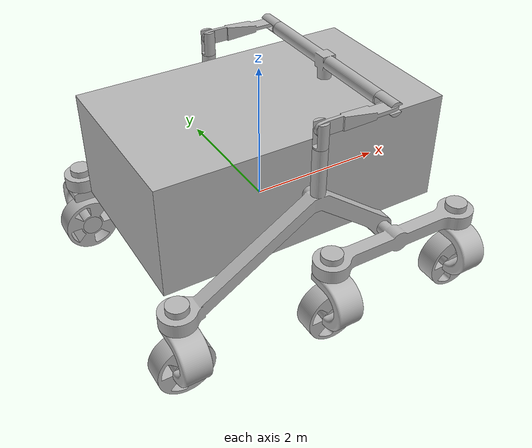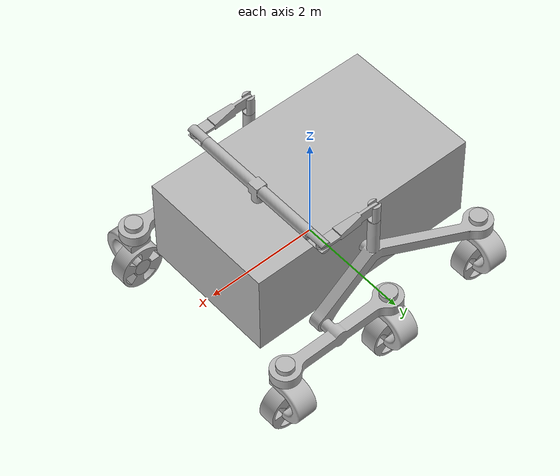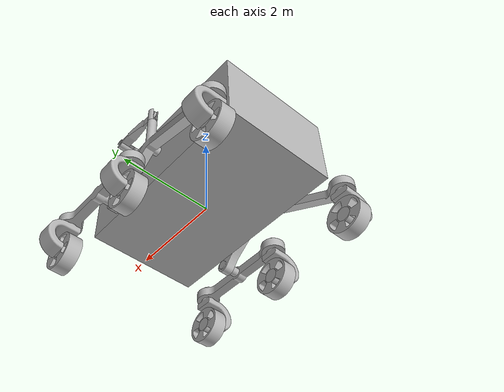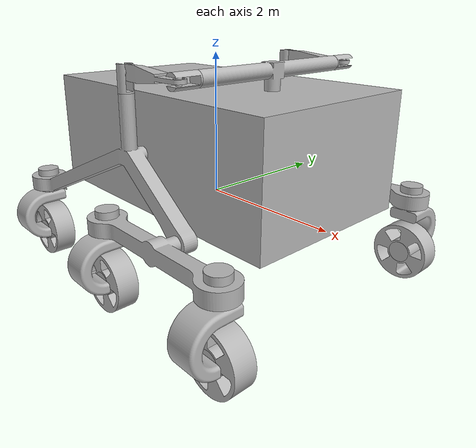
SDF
<?xml version='1.0'?>
<sdf version='1.7'>

  <model name='rover_one'>
    <link name='base_link'>
      <inertial>
        <pose>0 0 0.8 0 -0 0</pose>
        <mass>5</mass>
        <inertia>
          <ixx>3.67083</ixx>
          <ixy>0</ixy>
          <ixz>0</ixz>
          <iyy>8.41665</iyy>
          <iyz>0</iyz>
          <izz>9.95415</izz>
        </inertia>
      </inertial>
      <self_collide>0</self_collide>
      <enable_wind>0</enable_wind>
      <kinematic>0</kinematic>
      <pose>0 0 0 0 -0 0</pose>
      <visual name='base_link_fixed_joint_lump__body_visual'>
        <pose>0 0 0 0 -0 0</pose>
        <geometry>
          <mesh>
            <scale>0.01 0.01 0.01</scale>
            <uri>/home/user/Rover-Sim/rover_sim/meshes/body.stl</uri>
          </mesh>
        </geometry>
        <material>
          <shader type='pixel'/>
          <emissive>0 0 0 1</emissive>
        </material>
        <transparency>0</transparency>
        <cast_shadows>1</cast_shadows>
      </visual>
      <collision name='base_link_fixed_joint_lump__body_collision'>
        <laser_retro>0</laser_retro>
        <max_contacts>10</max_contacts>
        <pose>0 0 0 0 -0 0</pose>
        <geometry>
          <mesh>
            <uri>/home/user/Rover-Sim/rover_sim/meshes/body.stl</uri>
            <scale>0.01 0.01 0.01</scale>
          </mesh>
        </geometry>
        <surface>
          <friction>
            <ode>
              <mu>1</mu>
              <mu2>1</mu2>
              <fdir1>0 0 0</fdir1>
              <slip1>0</slip1>
              <slip2>0</slip2>
            </ode>
            <torsional>
              <coefficient>1</coefficient>
              <patch_radius>0</patch_radius>
              <surface_radius>0</surface_radius>
              <use_patch_radius>1</use_patch_radius>
              <ode>
                <slip>0</slip>
              </ode>
            </torsional>
          </friction>
          <bounce>
            <restitution_coefficient>0</restitution_coefficient>
            <threshold>1e+06</threshold>
          </bounce>
          <contact>
            <collide_without_contact>0</collide_without_contact>
            <collide_without_contact_bitmask>1</collide_without_contact_bitmask>
            <collide_bitmask>1</collide_bitmask>
            <ode>
              <soft_cfm>0</soft_cfm>
              <soft_erp>0.2</soft_erp>
              <kp>1e+13</kp>
              <kd>1</kd>
              <max_vel>0.01</max_vel>
              <min_depth>0</min_depth>
            </ode>
            <bullet>
              <split_impulse>1</split_impulse>
              <split_impulse_penetration_threshold>-0.01</split_impulse_penetration_threshold>
              <soft_cfm>0</soft_cfm>
              <soft_erp>0.2</soft_erp>
              <kp>1e+13</kp>
              <kd>1</kd>
            </bullet>
          </contact>
        </surface>
      </collision>
    </link>
    <link name='diff_bar'>
      <pose>1.05 -0 1.6 0 -0 0</pose>
      <inertial>
        <pose>0 0 0.2 0 -0 0</pose>
        <mass>0.625</mass>
        <inertia>
          <ixx>0.502083</ixx>
          <ixy>0</ixy>
          <ixz>0</ixz>
          <iyy>0.0125</iyy>
          <iyz>0</iyz>
          <izz>0.502083</izz>
        </inertia>
      </inertial>
      <self_collide>0</self_collide>
      <enable_wind>0</enable_wind>
      <kinematic>0</kinematic>
      <visual name='diff_bar_visual'>
        <pose>0 0 -0.2 0 -0 0</pose>
        <geometry>
          <mesh>
            <scale>0.01 0.01 0.01</scale>
            <uri>/home/user/Rover-Sim/rover_sim/meshes/diff_bar.stl</uri>
          </mesh>
        </geometry>
        <material>
          <shader type='pixel'/>
          <emissive>0 0 0 1</emissive>
        </material>
        <transparency>0</transparency>
        <cast_shadows>1</cast_shadows>
      </visual>
      <collision name='diff_bar_collision'>
        <laser_retro>0</laser_retro>
        <max_contacts>10</max_contacts>
        <pose>0 0 -0.2 0 -0 0</pose>
        <geometry>
          <mesh>
            <uri>/home/user/Rover-Sim/rover_sim/meshes/diff_bar.stl</uri>
            <scale>0.01 0.01 0.01</scale>
          </mesh>
        </geometry>
        <surface>
          <friction>
            <ode>
              <mu>1</mu>
              <mu2>1</mu2>
              <fdir1>0 0 0</fdir1>
              <slip1>0</slip1>
              <slip2>0</slip2>
            </ode>
            <torsional>
              <coefficient>1</coefficient>
              <patch_radius>0</patch_radius>
              <surface_radius>0</surface_radius>
              <use_patch_radius>1</use_patch_radius>
              <ode>
                <slip>0</slip>
              </ode>
            </torsional>
          </friction>
          <bounce>
            <restitution_coefficient>0</restitution_coefficient>
            <threshold>1e+06</threshold>
          </bounce>
          <contact>
            <collide_without_contact>0</collide_without_contact>
            <collide_without_contact_bitmask>1</collide_without_contact_bitmask>
            <collide_bitmask>1</collide_bitmask>
            <ode>
              <soft_cfm>0</soft_cfm>
              <soft_erp>0.2</soft_erp>
              <kp>1e+13</kp>
              <kd>1</kd>
              <max_vel>0.01</max_vel>
              <min_depth>0</min_depth>
            </ode>
            <bullet>
              <split_impulse>1</split_impulse>
              <split_impulse_penetration_threshold>-0.01</split_impulse_penetration_threshold>
              <soft_cfm>0</soft_cfm>
              <soft_erp>0.2</soft_erp>
              <kp>1e+13</kp>
              <kd>1</kd>
            </bullet>
          </contact>
        </surface>
      </collision>
    </link>
    <link name='left_bogie'>
      <pose>1.05 -1.55 -0 0 -0 0</pose>
      <inertial>
        <pose>0 -0.28 0 0 -0 0</pose>
        <mass>1.25</mass>
        <inertia>
          <ixx>0.0356771</ixx>
          <ixy>0</ixy>
          <ixz>0</ixz>
          <iyy>0.708333</iyy>
          <iyz>0</iyz>
          <izz>0.735677</izz>
        </inertia>
      </inertial>
      <self_collide>0</self_collide>
      <enable_wind>0</enable_wind>
      <kinematic>0</kinematic>
      <visual name='left_bogie_visual'>
        <pose>0 -0.18 0 0 -0 0</pose>
        <geometry>
          <mesh>
            <scale>0.01 0.01 0.01</scale>
            <uri>/home/user/Rover-Sim/rover_sim/meshes/bogie.stl</uri>
          </mesh>
        </geometry>
        <material>
          <shader type='pixel'/>
        </material>
        <transparency>0</transparency>
        <cast_shadows>1</cast_shadows>
      </visual>
      <collision name='left_bogie_collision'>
        <laser_retro>0</laser_retro>
        <max_contacts>10</max_contacts>
        <pose>0 -0.18 0 0 -0 0</pose>
        <geometry>
          <mesh>
            <uri>/home/user/Rover-Sim/rover_sim/meshes/bogie.stl</uri>
            <scale>0.01 0.01 0.01</scale>
          </mesh>
        </geometry>
        <surface>
          <friction>
            <ode>
              <mu>1</mu>
              <mu2>1</mu2>
              <fdir1>0 0 0</fdir1>
              <slip1>0</slip1>
              <slip2>0</slip2>
            </ode>
            <torsional>
              <coefficient>1</coefficient>
              <patch_radius>0</patch_radius>
              <surface_radius>0</surface_radius>
              <use_patch_radius>1</use_patch_radius>
              <ode>
                <slip>0</slip>
              </ode>
            </torsional>
          </friction>
          <bounce>
            <restitution_coefficient>0</restitution_coefficient>
            <threshold>1e+06</threshold>
          </bounce>
          <contact>
            <collide_without_contact>0</collide_without_contact>
            <collide_without_contact_bitmask>1</collide_without_contact_bitmask>
            <collide_bitmask>1</collide_bitmask>
            <ode>
              <soft_cfm>0</soft_cfm>
              <soft_erp>0.2</soft_erp>
              <kp>1e+13</kp>
              <kd>1</kd>
              <max_vel>0.01</max_vel>
              <min_depth>0</min_depth>
            </ode>
            <bullet>
              <split_impulse>1</split_impulse>
              <split_impulse_penetration_threshold>-0.01</split_impulse_penetration_threshold>
              <soft_cfm>0</soft_cfm>
              <soft_erp>0.2</soft_erp>
              <kp>1e+13</kp>
              <kd>1</kd>
            </bullet>
          </contact>
        </surface>
      </collision>
    </link>
    <link name='left_rocker'>
      <pose>-0 -1.25 0.8 0 -0 0</pose>
      <inertial>
        <pose>0 -0.3 0 0 -0 0</pose>
        <mass>2.5</mass>
        <inertia>
          <ixx>0.24375</ixx>
          <ixy>0</ixy>
          <ixz>0</ixz>
          <iyy>2.30208</iyy>
          <iyz>0</iyz>
          <izz>2.20833</izz>
        </inertia>
      </inertial>
      <self_collide>0</self_collide>
      <enable_wind>0</enable_wind>
      <kinematic>0</kinematic>
      <visual name='left_rocker_visual'>
        <pose>0 -0.1 0 0 -0 0</pose>
        <geometry>
          <mesh>
            <scale>0.01 0.01 0.01</scale>
            <uri>/home/user/Rover-Sim/rover_sim/meshes/rocker.stl</uri>
          </mesh>
        </geometry>
        <material>
          <shader type='pixel'/>
        </material>
        <transparency>0</transparency>
        <cast_shadows>1</cast_shadows>
      </visual>
      <collision name='left_rocker_collision'>
        <laser_retro>0</laser_retro>
        <max_contacts>10</max_contacts>
        <pose>0 -0.1 0 0 -0 0</pose>
        <geometry>
          <mesh>
            <uri>/home/user/Rover-Sim/rover_sim/meshes/rocker.stl</uri>
            <scale>0.01 0.01 0.01</scale>
          </mesh>
        </geometry>
        <surface>
          <friction>
            <ode>
              <mu>1</mu>
              <mu2>1</mu2>
              <fdir1>0 0 0</fdir1>
              <slip1>0</slip1>
              <slip2>0</slip2>
            </ode>
            <torsional>
              <coefficient>1</coefficient>
              <patch_radius>0</patch_radius>
              <surface_radius>0</surface_radius>
              <use_patch_radius>1</use_patch_radius>
              <ode>
                <slip>0</slip>
              </ode>
            </torsional>
          </friction>
          <bounce>
            <restitution_coefficient>0</restitution_coefficient>
            <threshold>1e+06</threshold>
          </bounce>
          <contact>
            <collide_without_contact>0</collide_without_contact>
            <collide_without_contact_bitmask>1</collide_without_contact_bitmask>
            <collide_bitmask>1</collide_bitmask>
            <ode>
              <soft_cfm>0</soft_cfm>
              <soft_erp>0.2</soft_erp>
              <kp>1e+13</kp>
              <kd>1</kd>
              <max_vel>0.01</max_vel>
              <min_depth>0</min_depth>
            </ode>
            <bullet>
              <split_impulse>1</split_impulse>
              <split_impulse_penetration_threshold>-0.01</split_impulse_penetration_threshold>
              <soft_cfm>0</soft_cfm>
              <soft_erp>0.2</soft_erp>
              <kp>1e+13</kp>
              <kd>1</kd>
            </bullet>
          </contact>
        </surface>
      </collision>
    </link>
    <link name='link_left'>
      <pose>0 -1.45 1.85 0 -0 0</pose>
      <inertial>
        <pose>0 0 0 0 -0 0</pose>
        <mass>0.5</mass>
        <inertia>
          <ixx>0.00333333</ixx>
          <ixy>0</ixy>
          <ixz>0</ixz>
          <iyy>0.0667708</iyy>
          <iyz>0</iyz>
          <izz>0.00333333</izz>
        </inertia>
      </inertial>
      <self_collide>0</self_collide>
      <enable_wind>0</enable_wind>
      <kinematic>0</kinematic>
      <visual name='link_left_visual'>
        <pose>0.1 -0.05 0.1 0 -0 0</pose>
        <geometry>
          <mesh>
            <scale>0.01 0.01 0.01</scale>
            <uri>/home/user/Rover-Sim/rover_sim/meshes/link.stl</uri>
          </mesh>
        </geometry>
        <material>
          <shader type='pixel'/>
          <emissive>0 0 0 1</emissive>
        </material>
        <transparency>0</transparency>
        <cast_shadows>1</cast_shadows>
      </visual>
      <collision name='link_left_collision'>
        <laser_retro>0</laser_retro>
        <max_contacts>10</max_contacts>
        <pose>0.1 -0.05 0.1 0 -0 0</pose>
        <geometry>
          <mesh>
            <uri>/home/user/Rover-Sim/rover_sim/meshes/link.stl</uri>
            <scale>0.01 0.01 0.01</scale>
          </mesh>
        </geometry>
        <surface>
          <friction>
            <ode>
              <mu>1</mu>
              <mu2>1</mu2>
              <fdir1>0 0 0</fdir1>
              <slip1>0</slip1>
              <slip2>0</slip2>
            </ode>
            <torsional>
              <coefficient>1</coefficient>
              <patch_radius>0</patch_radius>
              <surface_radius>0</surface_radius>
              <use_patch_radius>1</use_patch_radius>
              <ode>
                <slip>0</slip>
              </ode>
            </torsional>
          </friction>
          <bounce>
            <restitution_coefficient>0</restitution_coefficient>
            <threshold>1e+06</threshold>
          </bounce>
          <contact>
            <collide_without_contact>0</collide_without_contact>
            <collide_without_contact_bitmask>1</collide_without_contact_bitmask>
            <collide_bitmask>1</collide_bitmask>
            <ode>
              <soft_cfm>0</soft_cfm>
              <soft_erp>0.2</soft_erp>
              <kp>1e+13</kp>
              <kd>1</kd>
              <max_vel>0.01</max_vel>
              <min_depth>0</min_depth>
            </ode>
            <bullet>
              <split_impulse>1</split_impulse>
              <split_impulse_penetration_threshold>-0.01</split_impulse_penetration_threshold>
              <soft_cfm>0</soft_cfm>
              <soft_erp>0.2</soft_erp>
              <kp>1e+13</kp>
              <kd>1</kd>
            </bullet>
          </contact>
        </surface>
      </collision>
    </link>
    <link name='link_right'>
      <pose>0 1.45 1.85 0 -0 0</pose>
      <inertial>
        <pose>0 0 0 0 -0 0</pose>
        <mass>0.5</mass>
        <inertia>
          <ixx>0.00333333</ixx>
          <ixy>0</ixy>
          <ixz>0</ixz>
          <iyy>0.0667708</iyy>
          <iyz>0</iyz>
          <izz>0.00333333</izz>
        </inertia>
      </inertial>
      <self_collide>0</self_collide>
      <enable_wind>0</enable_wind>
      <kinematic>0</kinematic>
      <visual name='link_right_visual'>
        <pose>0.1 -0.05 0.1 0 -0 0</pose>
        <geometry>
          <mesh>
            <scale>0.01 0.01 0.01</scale>
            <uri>/home/user/Rover-Sim/rover_sim/meshes/link.stl</uri>
          </mesh>
        </geometry>
        <material>
          <shader type='pixel'/>
          <emissive>0 0 0 1</emissive>
        </material>
        <transparency>0</transparency>
        <cast_shadows>1</cast_shadows>
      </visual>
      <collision name='link_right_collision'>
        <laser_retro>0</laser_retro>
        <max_contacts>10</max_contacts>
        <pose>0.1 -0.05 0.1 0 -0 0</pose>
        <geometry>
          <mesh>
            <uri>/home/user/Rover-Sim/rover_sim/meshes/link.stl</uri>
            <scale>0.01 0.01 0.01</scale>
          </mesh>
        </geometry>
        <surface>
          <friction>
            <ode>
              <mu>1</mu>
              <mu2>1</mu2>
              <fdir1>0 0 0</fdir1>
              <slip1>0</slip1>
              <slip2>0</slip2>
            </ode>
            <torsional>
              <coefficient>1</coefficient>
              <patch_radius>0</patch_radius>
              <surface_radius>0</surface_radius>
              <use_patch_radius>1</use_patch_radius>
              <ode>
                <slip>0</slip>
              </ode>
            </torsional>
          </friction>
          <bounce>
            <restitution_coefficient>0</restitution_coefficient>
            <threshold>1e+06</threshold>
          </bounce>
          <contact>
            <collide_without_contact>0</collide_without_contact>
            <collide_without_contact_bitmask>1</collide_without_contact_bitmask>
            <collide_bitmask>1</collide_bitmask>
            <ode>
              <soft_cfm>0</soft_cfm>
              <soft_erp>0.2</soft_erp>
              <kp>1e+13</kp>
              <kd>1</kd>
              <max_vel>0.01</max_vel>
              <min_depth>0</min_depth>
            </ode>
            <bullet>
              <split_impulse>1</split_impulse>
              <split_impulse_penetration_threshold>-0.01</split_impulse_penetration_threshold>
              <soft_cfm>0</soft_cfm>
              <soft_erp>0.2</soft_erp>
              <kp>1e+13</kp>
              <kd>1</kd>
            </bullet>
          </contact>
        </surface>
      </collision>
    </link>
    <link name='pivot_diff_bar_left'>
      <pose>1.05 -1.2 1.85 0 -0 0</pose>
      <inertial>
        <pose>0 0 0 0 -0 0</pose>
        <mass>0.2</mass>
        <inertia>
          <ixx>0.1</ixx>
          <ixy>0</ixy>
          <ixz>0</ixz>
          <iyy>0.1</iyy>
          <iyz>0</iyz>
          <izz>0.1</izz>
        </inertia>
      </inertial>
      <self_collide>0</self_collide>
      <enable_wind>0</enable_wind>
      <kinematic>0</kinematic>
      <visual name='pivot_diff_bar_left_visual'>
        <pose>0 -0.1 0 -1.57079 1.57079 3.14159</pose>
        <geometry>
          <mesh>
            <scale>0.01 0.01 0.01</scale>
            <uri>/home/user/Rover-Sim/rover_sim/meshes/pivot.stl</uri>
          </mesh>
        </geometry>
        <material>
          <shader type='pixel'/>
          <emissive>0 0 0 1</emissive>
        </material>
        <transparency>0</transparency>
        <cast_shadows>1</cast_shadows>
      </visual>
      <collision name='pivot_diff_bar_left_collision'>
        <laser_retro>0</laser_retro>
        <max_contacts>10</max_contacts>
        <pose>0 -0.1 0 -1.57079 1.57079 3.14159</pose>
        <geometry>
          <mesh>
            <uri>/home/user/Rover-Sim/rover_sim/meshes/pivot.stl</uri>
            <scale>0.01 0.01 0.01</scale>
          </mesh>
        </geometry>
        <surface>
          <friction>
            <ode>
              <mu>1</mu>
              <mu2>1</mu2>
              <fdir1>0 0 0</fdir1>
              <slip1>0</slip1>
              <slip2>0</slip2>
            </ode>
            <torsional>
              <coefficient>1</coefficient>
              <patch_radius>0</patch_radius>
              <surface_radius>0</surface_radius>
              <use_patch_radius>1</use_patch_radius>
              <ode>
                <slip>0</slip>
              </ode>
            </torsional>
          </friction>
          <bounce>
            <restitution_coefficient>0</restitution_coefficient>
            <threshold>1e+06</threshold>
          </bounce>
          <contact>
            <collide_without_contact>0</collide_without_contact>
            <collide_without_contact_bitmask>1</collide_without_contact_bitmask>
            <collide_bitmask>1</collide_bitmask>
            <ode>
              <soft_cfm>0</soft_cfm>
              <soft_erp>0.2</soft_erp>
              <kp>1e+13</kp>
              <kd>1</kd>
              <max_vel>0.01</max_vel>
              <min_depth>0</min_depth>
            </ode>
            <bullet>
              <split_impulse>1</split_impulse>
              <split_impulse_penetration_threshold>-0.01</split_impulse_penetration_threshold>
              <soft_cfm>0</soft_cfm>
              <soft_erp>0.2</soft_erp>
              <kp>1e+13</kp>
              <kd>1</kd>
            </bullet>
          </contact>
        </surface>
      </collision>
    </link>
    <link name='pivot_diff_bar_right'>
      <pose>1.05 1.2 1.85 0 -0 0</pose>
      <inertial>
        <pose>0 0 0 0 -0 0</pose>
        <mass>0.2</mass>
        <inertia>
          <ixx>0.1</ixx>
          <ixy>0</ixy>
          <ixz>0</ixz>
          <iyy>0.1</iyy>
          <iyz>0</iyz>
          <izz>0.1</izz>
        </inertia>
      </inertial>
      <self_collide>0</self_collide>
      <enable_wind>0</enable_wind>
      <kinematic>0</kinematic>
      <visual name='pivot_diff_bar_right_visual'>
        <pose>0 0.1 0 1.57079 1.57079 -3.14159</pose>
        <geometry>
          <mesh>
            <scale>0.01 0.01 0.01</scale>
            <uri>/home/user/Rover-Sim/rover_sim/meshes/pivot.stl</uri>
          </mesh>
        </geometry>
        <material>
          <shader type='pixel'/>
          <emissive>0 0 0 1</emissive>
        </material>
        <transparency>0</transparency>
        <cast_shadows>1</cast_shadows>
      </visual>
      <collision name='pivot_diff_bar_right_collision'>
        <laser_retro>0</laser_retro>
        <max_contacts>10</max_contacts>
        <pose>0 0.1 0 1.57079 1.57079 3.14159</pose>
        <geometry>
          <mesh>
            <uri>/home/user/Rover-Sim/rover_sim/meshes/pivot.stl</uri>
            <scale>0.01 0.01 0.01</scale>
          </mesh>
        </geometry>
        <surface>
          <friction>
            <ode>
              <mu>1</mu>
              <mu2>1</mu2>
              <fdir1>0 0 0</fdir1>
              <slip1>0</slip1>
              <slip2>0</slip2>
            </ode>
            <torsional>
              <coefficient>1</coefficient>
              <patch_radius>0</patch_radius>
              <surface_radius>0</surface_radius>
              <use_patch_radius>1</use_patch_radius>
              <ode>
                <slip>0</slip>
              </ode>
            </torsional>
          </friction>
          <bounce>
            <restitution_coefficient>0</restitution_coefficient>
            <threshold>1e+06</threshold>
          </bounce>
          <contact>
            <collide_without_contact>0</collide_without_contact>
            <collide_without_contact_bitmask>1</collide_without_contact_bitmask>
            <collide_bitmask>1</collide_bitmask>
            <ode>
              <soft_cfm>0</soft_cfm>
              <soft_erp>0.2</soft_erp>
              <kp>1e+13</kp>
              <kd>1</kd>
              <max_vel>0.01</max_vel>
              <min_depth>0</min_depth>
            </ode>
            <bullet>
              <split_impulse>1</split_impulse>
              <split_impulse_penetration_threshold>-0.01</split_impulse_penetration_threshold>
              <soft_cfm>0</soft_cfm>
              <soft_erp>0.2</soft_erp>
              <kp>1e+13</kp>
              <kd>1</kd>
            </bullet>
          </contact>
        </surface>
      </collision>
    </link>
    <link name='pivot_left_rocker'>
      <pose>-0 -1.45 1.6 0 -0 0</pose>
      <inertial>
        <pose>0 0 0 0 -0 0</pose>
        <mass>0.2</mass>
        <inertia>
          <ixx>0.1</ixx>
          <ixy>0</ixy>
          <ixz>0</ixz>
          <iyy>0.1</iyy>
          <iyz>0</iyz>
          <izz>0.1</izz>
        </inertia>
      </inertial>
      <self_collide>0</self_collide>
      <enable_wind>0</enable_wind>
      <kinematic>0</kinematic>
      <visual name='pivot_left_rocker_visual'>
        <pose>0 0 0.1 0 -0 1.57079</pose>
        <geometry>
          <mesh>
            <scale>0.01 0.01 0.01</scale>
            <uri>/home/user/Rover-Sim/rover_sim/meshes/pivot.stl</uri>
          </mesh>
        </geometry>
        <material>
          <shader type='pixel'/>
        </material>
        <transparency>0</transparency>
        <cast_shadows>1</cast_shadows>
      </visual>
      <collision name='pivot_left_rocker_collision'>
        <laser_retro>0</laser_retro>
        <max_contacts>10</max_contacts>
        <pose>0 0 0.1 0 -0 1.57079</pose>
        <geometry>
          <mesh>
            <uri>/home/user/Rover-Sim/rover_sim/meshes/pivot.stl</uri>
            <scale>0.01 0.01 0.01</scale>
          </mesh>
        </geometry>
        <surface>
          <friction>
            <ode>
              <mu>1</mu>
              <mu2>1</mu2>
              <fdir1>0 0 0</fdir1>
              <slip1>0</slip1>
              <slip2>0</slip2>
            </ode>
            <torsional>
              <coefficient>1</coefficient>
              <patch_radius>0</patch_radius>
              <surface_radius>0</surface_radius>
              <use_patch_radius>1</use_patch_radius>
              <ode>
                <slip>0</slip>
              </ode>
            </torsional>
          </friction>
          <bounce>
            <restitution_coefficient>0</restitution_coefficient>
            <threshold>1e+06</threshold>
          </bounce>
          <contact>
            <collide_without_contact>0</collide_without_contact>
            <collide_without_contact_bitmask>1</collide_without_contact_bitmask>
            <collide_bitmask>1</collide_bitmask>
            <ode>
              <soft_cfm>0</soft_cfm>
              <soft_erp>0.2</soft_erp>
              <kp>1e+13</kp>
              <kd>1</kd>
              <max_vel>0.01</max_vel>
              <min_depth>0</min_depth>
            </ode>
            <bullet>
              <split_impulse>1</split_impulse>
              <split_impulse_penetration_threshold>-0.01</split_impulse_penetration_threshold>
              <soft_cfm>0</soft_cfm>
              <soft_erp>0.2</soft_erp>
              <kp>1e+13</kp>
              <kd>1</kd>
            </bullet>
          </contact>
        </surface>
      </collision>
    </link>
    <link name='pivot_right_rocker'>
      <pose>0 1.45 1.6 0 -0 0</pose>
      <inertial>
        <pose>0 0 0 0 -0 0</pose>
        <mass>0.2</mass>
        <inertia>
          <ixx>0.1</ixx>
          <ixy>0</ixy>
          <ixz>0</ixz>
          <iyy>0.1</iyy>
          <iyz>0</iyz>
          <izz>0.1</izz>
        </inertia>
      </inertial>
      <self_collide>0</self_collide>
      <enable_wind>0</enable_wind>
      <kinematic>0</kinematic>
      <visual name='pivot_right_rocker_visual'>
        <pose>0 0 0.1 0 -0 1.57079</pose>
        <geometry>
          <mesh>
            <scale>0.01 0.01 0.01</scale>
            <uri>/home/user/Rover-Sim/rover_sim/meshes/pivot.stl</uri>
          </mesh>
        </geometry>
        <material>
          <shader type='pixel'/>
        </material>
        <transparency>0</transparency>
        <cast_shadows>1</cast_shadows>
      </visual>
      <collision name='pivot_right_rocker_collision'>
        <laser_retro>0</laser_retro>
        <max_contacts>10</max_contacts>
        <pose>0 0 0.1 0 -0 1.57079</pose>
        <geometry>
          <mesh>
            <uri>/home/user/Rover-Sim/rover_sim/meshes/pivot.stl</uri>
            <scale>0.01 0.01 0.01</scale>
          </mesh>
        </geometry>
        <surface>
          <friction>
            <ode>
              <mu>1</mu>
              <mu2>1</mu2>
              <fdir1>0 0 0</fdir1>
              <slip1>0</slip1>
              <slip2>0</slip2>
            </ode>
            <torsional>
              <coefficient>1</coefficient>
              <patch_radius>0</patch_radius>
              <surface_radius>0</surface_radius>
              <use_patch_radius>1</use_patch_radius>
              <ode>
                <slip>0</slip>
              </ode>
            </torsional>
          </friction>
          <bounce>
            <restitution_coefficient>0</restitution_coefficient>
            <threshold>1e+06</threshold>
          </bounce>
          <contact>
            <collide_without_contact>0</collide_without_contact>
            <collide_without_contact_bitmask>1</collide_without_contact_bitmask>
            <collide_bitmask>1</collide_bitmask>
            <ode>
              <soft_cfm>0</soft_cfm>
              <soft_erp>0.2</soft_erp>
              <kp>1e+13</kp>
              <kd>1</kd>
              <max_vel>0.01</max_vel>
              <min_depth>0</min_depth>
            </ode>
            <bullet>
              <split_impulse>1</split_impulse>
              <split_impulse_penetration_threshold>-0.01</split_impulse_penetration_threshold>
              <soft_cfm>0</soft_cfm>
              <soft_erp>0.2</soft_erp>
              <kp>1e+13</kp>
              <kd>1</kd>
            </bullet>
          </contact>
        </surface>
      </collision>
    </link>
    <link name='right_bogie'>
      <pose>1.05 1.55 -0 0 -0 0</pose>
      <inertial>
        <pose>0 0.28 0 0 -0 0</pose>
        <mass>1.25</mass>
        <inertia>
          <ixx>0.0356771</ixx>
          <ixy>0</ixy>
          <ixz>0</ixz>
          <iyy>0.708333</iyy>
          <iyz>0</iyz>
          <izz>0.735677</izz>
        </inertia>
      </inertial>
      <self_collide>0</self_collide>
      <enable_wind>0</enable_wind>
      <kinematic>0</kinematic>
      <visual name='right_bogie_visual'>
        <pose>0 0.18 0 0 -0 3.14159</pose>
        <geometry>
          <mesh>
            <scale>0.01 0.01 0.01</scale>
            <uri>/home/user/Rover-Sim/rover_sim/meshes/bogie.stl</uri>
          </mesh>
        </geometry>
        <material>
          <shader type='pixel'/>
        </material>
        <transparency>0</transparency>
        <cast_shadows>1</cast_shadows>
      </visual>
      <collision name='right_bogie_collision'>
        <laser_retro>0</laser_retro>
        <max_contacts>10</max_contacts>
        <pose>0 0.18 0 0 -0 3.14159</pose>
        <geometry>
          <mesh>
            <uri>/home/user/Rover-Sim/rover_sim/meshes/bogie.stl</uri>
            <scale>0.01 0.01 0.01</scale>
          </mesh>
        </geometry>
        <surface>
          <friction>
            <ode>
              <mu>1</mu>
              <mu2>1</mu2>
              <fdir1>0 0 0</fdir1>
              <slip1>0</slip1>
              <slip2>0</slip2>
            </ode>
            <torsional>
              <coefficient>1</coefficient>
              <patch_radius>0</patch_radius>
              <surface_radius>0</surface_radius>
              <use_patch_radius>1</use_patch_radius>
              <ode>
                <slip>0</slip>
              </ode>
            </torsional>
          </friction>
          <bounce>
            <restitution_coefficient>0</restitution_coefficient>
            <threshold>1e+06</threshold>
          </bounce>
          <contact>
            <collide_without_contact>0</collide_without_contact>
            <collide_without_contact_bitmask>1</collide_without_contact_bitmask>
            <collide_bitmask>1</collide_bitmask>
            <ode>
              <soft_cfm>0</soft_cfm>
              <soft_erp>0.2</soft_erp>
              <kp>1e+13</kp>
              <kd>1</kd>
              <max_vel>0.01</max_vel>
              <min_depth>0</min_depth>
            </ode>
            <bullet>
              <split_impulse>1</split_impulse>
              <split_impulse_penetration_threshold>-0.01</split_impulse_penetration_threshold>
              <soft_cfm>0</soft_cfm>
              <soft_erp>0.2</soft_erp>
              <kp>1e+13</kp>
              <kd>1</kd>
            </bullet>
          </contact>
        </surface>
      </collision>
    </link>
    <link name='right_rocker'>
      <pose>0 1.25 0.8 0 -0 0</pose>
      <inertial>
        <pose>0 0.3 0 0 -0 0</pose>
        <mass>2.5</mass>
        <inertia>
          <ixx>0.24375</ixx>
          <ixy>0</ixy>
          <ixz>0</ixz>
          <iyy>2.30208</iyy>
          <iyz>0</iyz>
          <izz>2.20833</izz>
        </inertia>
      </inertial>
      <self_collide>0</self_collide>
      <enable_wind>0</enable_wind>
      <kinematic>0</kinematic>
      <visual name='right_rocker_visual'>
        <pose>0 0.1 0 0 -0 0</pose>
        <geometry>
          <mesh>
            <scale>0.01 0.01 0.01</scale>
            <uri>/home/user/Rover-Sim/rover_sim/meshes/rocker_mirrored.stl</uri>
          </mesh>
        </geometry>
        <material>
          <shader type='pixel'/>
        </material>
        <transparency>0</transparency>
        <cast_shadows>1</cast_shadows>
      </visual>
      <collision name='right_rocker_collision'>
        <laser_retro>0</laser_retro>
        <max_contacts>10</max_contacts>
        <pose>0 0.1 0 0 -0 0</pose>
        <geometry>
          <mesh>
            <uri>/home/user/Rover-Sim/rover_sim/meshes/rocker_mirrored.stl</uri>
            <scale>0.01 0.01 0.01</scale>
          </mesh>
        </geometry>
        <surface>
          <friction>
            <ode>
              <mu>1</mu>
              <mu2>1</mu2>
              <fdir1>0 0 0</fdir1>
              <slip1>0</slip1>
              <slip2>0</slip2>
            </ode>
            <torsional>
              <coefficient>1</coefficient>
              <patch_radius>0</patch_radius>
              <surface_radius>0</surface_radius>
              <use_patch_radius>1</use_patch_radius>
              <ode>
                <slip>0</slip>
              </ode>
            </torsional>
          </friction>
          <bounce>
            <restitution_coefficient>0</restitution_coefficient>
            <threshold>1e+06</threshold>
          </bounce>
          <contact>
            <collide_without_contact>0</collide_without_contact>
            <collide_without_contact_bitmask>1</collide_without_contact_bitmask>
            <collide_bitmask>1</collide_bitmask>
            <ode>
              <soft_cfm>0</soft_cfm>
              <soft_erp>0.2</soft_erp>
              <kp>1e+13</kp>
              <kd>1</kd>
              <max_vel>0.01</max_vel>
              <min_depth>0</min_depth>
            </ode>
            <bullet>
              <split_impulse>1</split_impulse>
              <split_impulse_penetration_threshold>-0.01</split_impulse_penetration_threshold>
              <soft_cfm>0</soft_cfm>
              <soft_erp>0.2</soft_erp>
              <kp>1e+13</kp>
              <kd>1</kd>
            </bullet>
          </contact>
        </surface>
      </collision>
    </link>
    <link name='servo_mount_1'>
      <pose>-2.1 -1.65 0 0 -0 0</pose>
      <inertial>
        <pose>0 -0.15 -0.35 0 -0 0</pose>
        <mass>0.625</mass>
        <inertia>
          <ixx>0.0908854</ixx>
          <ixy>0</ixy>
          <ixz>0</ixz>
          <iyy>0.0772135</iyy>
          <iyz>0</iyz>
          <izz>0.0303385</izz>
        </inertia>
      </inertial>
      <self_collide>0</self_collide>
      <enable_wind>0</enable_wind>
      <kinematic>0</kinematic>
      <visual name='servo_mount_1_visual'>
        <pose>0 0 0.1 0 -0 0</pose>
        <geometry>
          <mesh>
            <scale>0.01 0.01 0.01</scale>
            <uri>/home/user/Rover-Sim/rover_sim/meshes/servo_mount.stl</uri>
          </mesh>
        </geometry>
        <material>
          <shader type='pixel'/>
        </material>
        <transparency>0</transparency>
        <cast_shadows>1</cast_shadows>
      </visual>
      <collision name='servo_mount_1_collision'>
        <laser_retro>0</laser_retro>
        <max_contacts>10</max_contacts>
        <pose>0 0 0.1 0 -0 0</pose>
        <geometry>
          <mesh>
            <uri>/home/user/Rover-Sim/rover_sim/meshes/servo_mount.stl</uri>
            <scale>0.01 0.01 0.01</scale>
          </mesh>
        </geometry>
        <surface>
          <friction>
            <ode>
              <mu>1</mu>
              <mu2>1</mu2>
              <fdir1>0 0 0</fdir1>
              <slip1>0</slip1>
              <slip2>0</slip2>
            </ode>
            <torsional>
              <coefficient>1</coefficient>
              <patch_radius>0</patch_radius>
              <surface_radius>0</surface_radius>
              <use_patch_radius>1</use_patch_radius>
              <ode>
                <slip>0</slip>
              </ode>
            </torsional>
          </friction>
          <bounce>
            <restitution_coefficient>0</restitution_coefficient>
            <threshold>1e+06</threshold>
          </bounce>
          <contact>
            <collide_without_contact>0</collide_without_contact>
            <collide_without_contact_bitmask>1</collide_without_contact_bitmask>
            <collide_bitmask>1</collide_bitmask>
            <ode>
              <soft_cfm>0</soft_cfm>
              <soft_erp>0.2</soft_erp>
              <kp>1e+13</kp>
              <kd>1</kd>
              <max_vel>0.01</max_vel>
              <min_depth>0</min_depth>
            </ode>
            <bullet>
              <split_impulse>1</split_impulse>
              <split_impulse_penetration_threshold>-0.01</split_impulse_penetration_threshold>
              <soft_cfm>0</soft_cfm>
              <soft_erp>0.2</soft_erp>
              <kp>1e+13</kp>
              <kd>1</kd>
            </bullet>
          </contact>
        </surface>
      </collision>
    </link>
    <link name='servo_mount_2'>
      <pose>0 -1.83 -0 0 -0 0</pose>
      <inertial>
        <pose>0 -0.15 -0.35 0 -0 0</pose>
        <mass>0.625</mass>
        <inertia>
          <ixx>0.0908854</ixx>
          <ixy>0</ixy>
          <ixz>0</ixz>
          <iyy>0.0772135</iyy>
          <iyz>0</iyz>
          <izz>0.0303385</izz>
        </inertia>
      </inertial>
      <self_collide>0</self_collide>
      <enable_wind>0</enable_wind>
      <kinematic>0</kinematic>
      <visual name='servo_mount_2_visual'>
        <pose>0 0 0.1 0 -0 0</pose>
        <geometry>
          <mesh>
            <scale>0.01 0.01 0.01</scale>
            <uri>/home/user/Rover-Sim/rover_sim/meshes/servo_mount.stl</uri>
          </mesh>
        </geometry>
        <material>
          <shader type='pixel'/>
        </material>
        <transparency>0</transparency>
        <cast_shadows>1</cast_shadows>
      </visual>
      <collision name='servo_mount_2_collision'>
        <laser_retro>0</laser_retro>
        <max_contacts>10</max_contacts>
        <pose>0 0 0.1 0 -0 0</pose>
        <geometry>
          <mesh>
            <uri>/home/user/Rover-Sim/rover_sim/meshes/servo_mount.stl</uri>
            <scale>0.01 0.01 0.01</scale>
          </mesh>
        </geometry>
        <surface>
          <friction>
            <ode>
              <mu>1</mu>
              <mu2>1</mu2>
              <fdir1>0 0 0</fdir1>
              <slip1>0</slip1>
              <slip2>0</slip2>
            </ode>
            <torsional>
              <coefficient>1</coefficient>
              <patch_radius>0</patch_radius>
              <surface_radius>0</surface_radius>
              <use_patch_radius>1</use_patch_radius>
              <ode>
                <slip>0</slip>
              </ode>
            </torsional>
          </friction>
          <bounce>
            <restitution_coefficient>0</restitution_coefficient>
            <threshold>1e+06</threshold>
          </bounce>
          <contact>
            <collide_without_contact>0</collide_without_contact>
            <collide_without_contact_bitmask>1</collide_without_contact_bitmask>
            <collide_bitmask>1</collide_bitmask>
            <ode>
              <soft_cfm>0</soft_cfm>
              <soft_erp>0.2</soft_erp>
              <kp>1e+13</kp>
              <kd>1</kd>
              <max_vel>0.01</max_vel>
              <min_depth>0</min_depth>
            </ode>
            <bullet>
              <split_impulse>1</split_impulse>
              <split_impulse_penetration_threshold>-0.01</split_impulse_penetration_threshold>
              <soft_cfm>0</soft_cfm>
              <soft_erp>0.2</soft_erp>
              <kp>1e+13</kp>
              <kd>1</kd>
            </bullet>
          </contact>
        </surface>
      </collision>
    </link>
    <link name='servo_mount_3'>
      <pose>2.1 -1.83 -0 0 -0 0</pose>
      <inertial>
        <pose>0 -0.15 -0.35 0 -0 0</pose>
        <mass>0.625</mass>
        <inertia>
          <ixx>0.0908854</ixx>
          <ixy>0</ixy>
          <ixz>0</ixz>
          <iyy>0.0772135</iyy>
          <iyz>0</iyz>
          <izz>0.0303385</izz>
        </inertia>
      </inertial>
      <self_collide>0</self_collide>
      <enable_wind>0</enable_wind>
      <kinematic>0</kinematic>
      <visual name='servo_mount_3_visual'>
        <pose>0 0 0.1 0 -0 0</pose>
        <geometry>
          <mesh>
            <scale>0.01 0.01 0.01</scale>
            <uri>/home/user/Rover-Sim/rover_sim/meshes/servo_mount.stl</uri>
          </mesh>
        </geometry>
        <material>
          <shader type='pixel'/>
        </material>
        <transparency>0</transparency>
        <cast_shadows>1</cast_shadows>
      </visual>
      <collision name='servo_mount_3_collision'>
        <laser_retro>0</laser_retro>
        <max_contacts>10</max_contacts>
        <pose>0 0 0.1 0 -0 0</pose>
        <geometry>
          <mesh>
            <uri>/home/user/Rover-Sim/rover_sim/meshes/servo_mount.stl</uri>
            <scale>0.01 0.01 0.01</scale>
          </mesh>
        </geometry>
        <surface>
          <friction>
            <ode>
              <mu>1</mu>
              <mu2>1</mu2>
              <fdir1>0 0 0</fdir1>
              <slip1>0</slip1>
              <slip2>0</slip2>
            </ode>
            <torsional>
              <coefficient>1</coefficient>
              <patch_radius>0</patch_radius>
              <surface_radius>0</surface_radius>
              <use_patch_radius>1</use_patch_radius>
              <ode>
                <slip>0</slip>
              </ode>
            </torsional>
          </friction>
          <bounce>
            <restitution_coefficient>0</restitution_coefficient>
            <threshold>1e+06</threshold>
          </bounce>
          <contact>
            <collide_without_contact>0</collide_without_contact>
            <collide_without_contact_bitmask>1</collide_without_contact_bitmask>
            <collide_bitmask>1</collide_bitmask>
            <ode>
              <soft_cfm>0</soft_cfm>
              <soft_erp>0.2</soft_erp>
              <kp>1e+13</kp>
              <kd>1</kd>
              <max_vel>0.01</max_vel>
              <min_depth>0</min_depth>
            </ode>
            <bullet>
              <split_impulse>1</split_impulse>
              <split_impulse_penetration_threshold>-0.01</split_impulse_penetration_threshold>
              <soft_cfm>0</soft_cfm>
              <soft_erp>0.2</soft_erp>
              <kp>1e+13</kp>
              <kd>1</kd>
            </bullet>
          </contact>
        </surface>
      </collision>
    </link>
    <link name='servo_mount_4'>
      <pose>-2.1 1.65 0 0 -0 0</pose>
      <inertial>
        <pose>0 0.15 -0.35 0 -0 0</pose>
        <mass>0.625</mass>
        <inertia>
          <ixx>0.0908854</ixx>
          <ixy>0</ixy>
          <ixz>0</ixz>
          <iyy>0.0772135</iyy>
          <iyz>0</iyz>
          <izz>0.0303385</izz>
        </inertia>
      </inertial>
      <self_collide>0</self_collide>
      <enable_wind>0</enable_wind>
      <kinematic>0</kinematic>
      <visual name='servo_mount_4_visual'>
        <pose>0 0 0.1 0 -0 3.14159</pose>
        <geometry>
          <mesh>
            <scale>0.01 0.01 0.01</scale>
            <uri>/home/user/Rover-Sim/rover_sim/meshes/servo_mount.stl</uri>
          </mesh>
        </geometry>
        <material>
          <shader type='pixel'/>
        </material>
        <transparency>0</transparency>
        <cast_shadows>1</cast_shadows>
      </visual>
      <collision name='servo_mount_4_collision'>
        <laser_retro>0</laser_retro>
        <max_contacts>10</max_contacts>
        <pose>0 0 0.1 0 -0 3.14159</pose>
        <geometry>
          <mesh>
            <uri>/home/user/Rover-Sim/rover_sim/meshes/servo_mount.stl</uri>
            <scale>0.01 0.01 0.01</scale>
          </mesh>
        </geometry>
        <surface>
          <friction>
            <ode>
              <mu>1</mu>
              <mu2>1</mu2>
              <fdir1>0 0 0</fdir1>
              <slip1>0</slip1>
              <slip2>0</slip2>
            </ode>
            <torsional>
              <coefficient>1</coefficient>
              <patch_radius>0</patch_radius>
              <surface_radius>0</surface_radius>
              <use_patch_radius>1</use_patch_radius>
              <ode>
                <slip>0</slip>
              </ode>
            </torsional>
          </friction>
          <bounce>
            <restitution_coefficient>0</restitution_coefficient>
            <threshold>1e+06</threshold>
          </bounce>
          <contact>
            <collide_without_contact>0</collide_without_contact>
            <collide_without_contact_bitmask>1</collide_without_contact_bitmask>
            <collide_bitmask>1</collide_bitmask>
            <ode>
              <soft_cfm>0</soft_cfm>
              <soft_erp>0.2</soft_erp>
              <kp>1e+13</kp>
              <kd>1</kd>
              <max_vel>0.01</max_vel>
              <min_depth>0</min_depth>
            </ode>
            <bullet>
              <split_impulse>1</split_impulse>
              <split_impulse_penetration_threshold>-0.01</split_impulse_penetration_threshold>
              <soft_cfm>0</soft_cfm>
              <soft_erp>0.2</soft_erp>
              <kp>1e+13</kp>
              <kd>1</kd>
            </bullet>
          </contact>
        </surface>
      </collision>
    </link>
    <link name='servo_mount_5'>
      <pose>-0 1.83 0 0 -0 0</pose>
      <inertial>
        <pose>0 0.15 -0.35 0 -0 0</pose>
        <mass>0.625</mass>
        <inertia>
          <ixx>0.0908854</ixx>
          <ixy>0</ixy>
          <ixz>0</ixz>
          <iyy>0.0772135</iyy>
          <iyz>0</iyz>
          <izz>0.0303385</izz>
        </inertia>
      </inertial>
      <self_collide>0</self_collide>
      <enable_wind>0</enable_wind>
      <kinematic>0</kinematic>
      <visual name='servo_mount_5_visual'>
        <pose>0 0 0.1 0 -0 3.14159</pose>
        <geometry>
          <mesh>
            <scale>0.01 0.01 0.01</scale>
            <uri>/home/user/Rover-Sim/rover_sim/meshes/servo_mount.stl</uri>
          </mesh>
        </geometry>
        <material>
          <shader type='pixel'/>
        </material>
        <transparency>0</transparency>
        <cast_shadows>1</cast_shadows>
      </visual>
      <collision name='servo_mount_5_collision'>
        <laser_retro>0</laser_retro>
        <max_contacts>10</max_contacts>
        <pose>0 0 0.1 0 -0 3.14159</pose>
        <geometry>
          <mesh>
            <uri>/home/user/Rover-Sim/rover_sim/meshes/servo_mount.stl</uri>
            <scale>0.01 0.01 0.01</scale>
          </mesh>
        </geometry>
        <surface>
          <friction>
            <ode>
              <mu>1</mu>
              <mu2>1</mu2>
              <fdir1>0 0 0</fdir1>
              <slip1>0</slip1>
              <slip2>0</slip2>
            </ode>
            <torsional>
              <coefficient>1</coefficient>
              <patch_radius>0</patch_radius>
              <surface_radius>0</surface_radius>
              <use_patch_radius>1</use_patch_radius>
              <ode>
                <slip>0</slip>
              </ode>
            </torsional>
          </friction>
          <bounce>
            <restitution_coefficient>0</restitution_coefficient>
            <threshold>1e+06</threshold>
          </bounce>
          <contact>
            <collide_without_contact>0</collide_without_contact>
            <collide_without_contact_bitmask>1</collide_without_contact_bitmask>
            <collide_bitmask>1</collide_bitmask>
            <ode>
              <soft_cfm>0</soft_cfm>
              <soft_erp>0.2</soft_erp>
              <kp>1e+13</kp>
              <kd>1</kd>
              <max_vel>0.01</max_vel>
              <min_depth>0</min_depth>
            </ode>
            <bullet>
              <split_impulse>1</split_impulse>
              <split_impulse_penetration_threshold>-0.01</split_impulse_penetration_threshold>
              <soft_cfm>0</soft_cfm>
              <soft_erp>0.2</soft_erp>
              <kp>1e+13</kp>
              <kd>1</kd>
            </bullet>
          </contact>
        </surface>
      </collision>
    </link>
    <link name='servo_mount_6'>
      <pose>2.1 1.83 -0 0 -0 0</pose>
      <inertial>
        <pose>0 0.15 -0.35 0 -0 0</pose>
        <mass>0.625</mass>
        <inertia>
          <ixx>0.0908854</ixx>
          <ixy>0</ixy>
          <ixz>0</ixz>
          <iyy>0.0772135</iyy>
          <iyz>0</iyz>
          <izz>0.0303385</izz>
        </inertia>
      </inertial>
      <self_collide>0</self_collide>
      <enable_wind>0</enable_wind>
      <kinematic>0</kinematic>
      <visual name='servo_mount_6_visual'>
        <pose>0 0 0.1 0 -0 3.14159</pose>
        <geometry>
          <mesh>
            <scale>0.01 0.01 0.01</scale>
            <uri>/home/user/Rover-Sim/rover_sim/meshes/servo_mount.stl</uri>
          </mesh>
        </geometry>
        <material>
          <shader type='pixel'/>
        </material>
        <transparency>0</transparency>
        <cast_shadows>1</cast_shadows>
      </visual>
      <collision name='servo_mount_6_collision'>
        <laser_retro>0</laser_retro>
        <max_contacts>10</max_contacts>
        <pose>0 0 0.1 0 -0 3.14159</pose>
        <geometry>
          <mesh>
            <uri>/home/user/Rover-Sim/rover_sim/meshes/servo_mount.stl</uri>
            <scale>0.01 0.01 0.01</scale>
          </mesh>
        </geometry>
        <surface>
          <friction>
            <ode>
              <mu>1</mu>
              <mu2>1</mu2>
              <fdir1>0 0 0</fdir1>
              <slip1>0</slip1>
              <slip2>0</slip2>
            </ode>
            <torsional>
              <coefficient>1</coefficient>
              <patch_radius>0</patch_radius>
              <surface_radius>0</surface_radius>
              <use_patch_radius>1</use_patch_radius>
              <ode>
                <slip>0</slip>
              </ode>
            </torsional>
          </friction>
          <bounce>
            <restitution_coefficient>0</restitution_coefficient>
            <threshold>1e+06</threshold>
          </bounce>
          <contact>
            <collide_without_contact>0</collide_without_contact>
            <collide_without_contact_bitmask>1</collide_without_contact_bitmask>
            <collide_bitmask>1</collide_bitmask>
            <ode>
              <soft_cfm>0</soft_cfm>
              <soft_erp>0.2</soft_erp>
              <kp>1e+13</kp>
              <kd>1</kd>
              <max_vel>0.01</max_vel>
              <min_depth>0</min_depth>
            </ode>
            <bullet>
              <split_impulse>1</split_impulse>
              <split_impulse_penetration_threshold>-0.01</split_impulse_penetration_threshold>
              <soft_cfm>0</soft_cfm>
              <soft_erp>0.2</soft_erp>
              <kp>1e+13</kp>
              <kd>1</kd>
            </bullet>
          </contact>
        </surface>
      </collision>
    </link>
    <link name='wheel_1'>
      <pose>-2.1 -1.8 -0.8 0 -0 0</pose>
      <inertial>
        <pose>0 0.15 0 0 -0 0</pose>
        <mass>0.5</mass>
        <inertia>
          <ixx>0.02375</ixx>
          <ixy>0</ixy>
          <ixz>0</ixz>
          <iyy>0.04</iyy>
          <iyz>0</iyz>
          <izz>0.02375</izz>
        </inertia>
      </inertial>
      <self_collide>0</self_collide>
      <enable_wind>0</enable_wind>
      <kinematic>0</kinematic>
      <visual name='wheel_1_visual'>
        <pose>0 0 0 0 -0 0</pose>
        <geometry>
          <mesh>
            <scale>0.01 0.01 0.01</scale>
            <uri>/home/user/Rover-Sim/rover_sim/meshes/wheel.stl</uri>
          </mesh>
        </geometry>
        <material>
          <shader type='pixel'/>
        </material>
        <transparency>0</transparency>
        <cast_shadows>1</cast_shadows>
      </visual>
      <collision name='wheel_1_collision'>
        <laser_retro>0</laser_retro>
        <max_contacts>10</max_contacts>
        <pose>0 0 0 0 -0 0</pose>
        <geometry>
          <mesh>
            <uri>/home/user/Rover-Sim/rover_sim/meshes/wheel.stl</uri>
            <scale>0.01 0.01 0.01</scale>
          </mesh>
        </geometry>
        <surface>
          <friction>
            <ode>
              <mu>1</mu>
              <mu2>1</mu2>
              <fdir1>0 0 0</fdir1>
              <slip1>0</slip1>
              <slip2>0</slip2>
            </ode>
            <torsional>
              <coefficient>1</coefficient>
              <patch_radius>0</patch_radius>
              <surface_radius>0</surface_radius>
              <use_patch_radius>1</use_patch_radius>
              <ode>
                <slip>0</slip>
              </ode>
            </torsional>
          </friction>
          <bounce>
            <restitution_coefficient>0</restitution_coefficient>
            <threshold>1e+06</threshold>
          </bounce>
          <contact>
            <collide_without_contact>0</collide_without_contact>
            <collide_without_contact_bitmask>1</collide_without_contact_bitmask>
            <collide_bitmask>1</collide_bitmask>
            <ode>
              <soft_cfm>0</soft_cfm>
              <soft_erp>0.2</soft_erp>
              <kp>1e+13</kp>
              <kd>1</kd>
              <max_vel>0.01</max_vel>
              <min_depth>0</min_depth>
            </ode>
            <bullet>
              <split_impulse>1</split_impulse>
              <split_impulse_penetration_threshold>-0.01</split_impulse_penetration_threshold>
              <soft_cfm>0</soft_cfm>
              <soft_erp>0.2</soft_erp>
              <kp>1e+13</kp>
              <kd>1</kd>
            </bullet>
          </contact>
        </surface>
      </collision>
    </link>
    <link name='wheel_2'>
      <pose>0 -1.98 -0.8 0 -0 0</pose>
      <inertial>
        <pose>0 0.15 0 0 -0 0</pose>
        <mass>0.5</mass>
        <inertia>
          <ixx>0.02375</ixx>
          <ixy>0</ixy>
          <ixz>0</ixz>
          <iyy>0.04</iyy>
          <iyz>0</iyz>
          <izz>0.02375</izz>
        </inertia>
      </inertial>
      <self_collide>0</self_collide>
      <enable_wind>0</enable_wind>
      <kinematic>0</kinematic>
      <visual name='wheel_2_visual'>
        <pose>0 0 0 0 -0 0</pose>
        <geometry>
          <mesh>
            <scale>0.01 0.01 0.01</scale>
            <uri>/home/user/Rover-Sim/rover_sim/meshes/wheel.stl</uri>
          </mesh>
        </geometry>
        <material>
          <shader type='pixel'/>
        </material>
        <transparency>0</transparency>
        <cast_shadows>1</cast_shadows>
      </visual>
      <collision name='wheel_2_collision'>
        <laser_retro>0</laser_retro>
        <max_contacts>10</max_contacts>
        <pose>0 0 0 0 -0 0</pose>
        <geometry>
          <mesh>
            <uri>/home/user/Rover-Sim/rover_sim/meshes/wheel.stl</uri>
            <scale>0.01 0.01 0.01</scale>
          </mesh>
        </geometry>
        <surface>
          <friction>
            <ode>
              <mu>1</mu>
              <mu2>1</mu2>
              <fdir1>0 0 0</fdir1>
              <slip1>0</slip1>
              <slip2>0</slip2>
            </ode>
            <torsional>
              <coefficient>1</coefficient>
              <patch_radius>0</patch_radius>
              <surface_radius>0</surface_radius>
              <use_patch_radius>1</use_patch_radius>
              <ode>
                <slip>0</slip>
              </ode>
            </torsional>
          </friction>
          <bounce>
            <restitution_coefficient>0</restitution_coefficient>
            <threshold>1e+06</threshold>
          </bounce>
          <contact>
            <collide_without_contact>0</collide_without_contact>
            <collide_without_contact_bitmask>1</collide_without_contact_bitmask>
            <collide_bitmask>1</collide_bitmask>
            <ode>
              <soft_cfm>0</soft_cfm>
              <soft_erp>0.2</soft_erp>
              <kp>1e+13</kp>
              <kd>1</kd>
              <max_vel>0.01</max_vel>
              <min_depth>0</min_depth>
            </ode>
            <bullet>
              <split_impulse>1</split_impulse>
              <split_impulse_penetration_threshold>-0.01</split_impulse_penetration_threshold>
              <soft_cfm>0</soft_cfm>
              <soft_erp>0.2</soft_erp>
              <kp>1e+13</kp>
              <kd>1</kd>
            </bullet>
          </contact>
        </surface>
      </collision>
    </link>
    <link name='wheel_3'>
      <pose>2.1 -1.98 -0.8 0 -0 0</pose>
      <inertial>
        <pose>0 0.15 0 0 -0 0</pose>
        <mass>0.5</mass>
        <inertia>
          <ixx>0.02375</ixx>
          <ixy>0</ixy>
          <ixz>0</ixz>
          <iyy>0.04</iyy>
          <iyz>0</iyz>
          <izz>0.02375</izz>
        </inertia>
      </inertial>
      <self_collide>0</self_collide>
      <enable_wind>0</enable_wind>
      <kinematic>0</kinematic>
      <visual name='wheel_3_visual'>
        <pose>0 0 0 0 -0 0</pose>
        <geometry>
          <mesh>
            <scale>0.01 0.01 0.01</scale>
            <uri>/home/user/Rover-Sim/rover_sim/meshes/wheel.stl</uri>
          </mesh>
        </geometry>
        <material>
          <shader type='pixel'/>
        </material>
        <transparency>0</transparency>
        <cast_shadows>1</cast_shadows>
      </visual>
      <collision name='wheel_3_collision'>
        <laser_retro>0</laser_retro>
        <max_contacts>10</max_contacts>
        <pose>0 0 0 0 -0 0</pose>
        <geometry>
          <mesh>
            <uri>/home/user/Rover-Sim/rover_sim/meshes/wheel.stl</uri>
            <scale>0.01 0.01 0.01</scale>
          </mesh>
        </geometry>
        <surface>
          <friction>
            <ode>
              <mu>1</mu>
              <mu2>1</mu2>
              <fdir1>0 0 0</fdir1>
              <slip1>0</slip1>
              <slip2>0</slip2>
            </ode>
            <torsional>
              <coefficient>1</coefficient>
              <patch_radius>0</patch_radius>
              <surface_radius>0</surface_radius>
              <use_patch_radius>1</use_patch_radius>
              <ode>
                <slip>0</slip>
              </ode>
            </torsional>
          </friction>
          <bounce>
            <restitution_coefficient>0</restitution_coefficient>
            <threshold>1e+06</threshold>
          </bounce>
          <contact>
            <collide_without_contact>0</collide_without_contact>
            <collide_without_contact_bitmask>1</collide_without_contact_bitmask>
            <collide_bitmask>1</collide_bitmask>
            <ode>
              <soft_cfm>0</soft_cfm>
              <soft_erp>0.2</soft_erp>
              <kp>1e+13</kp>
              <kd>1</kd>
              <max_vel>0.01</max_vel>
              <min_depth>0</min_depth>
            </ode>
            <bullet>
              <split_impulse>1</split_impulse>
              <split_impulse_penetration_threshold>-0.01</split_impulse_penetration_threshold>
              <soft_cfm>0</soft_cfm>
              <soft_erp>0.2</soft_erp>
              <kp>1e+13</kp>
              <kd>1</kd>
            </bullet>
          </contact>
        </surface>
      </collision>
    </link>
    <link name='wheel_4'>
      <pose>-2.1 1.8 -0.8 0 -0 0</pose>
      <inertial>
        <pose>0 -0.15 0 0 -0 0</pose>
        <mass>0.5</mass>
        <inertia>
          <ixx>0.02375</ixx>
          <ixy>0</ixy>
          <ixz>0</ixz>
          <iyy>0.04</iyy>
          <iyz>0</iyz>
          <izz>0.02375</izz>
        </inertia>
      </inertial>
      <self_collide>0</self_collide>
      <enable_wind>0</enable_wind>
      <kinematic>0</kinematic>
      <visual name='wheel_4_visual'>
        <pose>0 0 0 0 -0 3.14159</pose>
        <geometry>
          <mesh>
            <scale>0.01 0.01 0.01</scale>
            <uri>/home/user/Rover-Sim/rover_sim/meshes/wheel.stl</uri>
          </mesh>
        </geometry>
        <material>
          <shader type='pixel'/>
        </material>
        <transparency>0</transparency>
        <cast_shadows>1</cast_shadows>
      </visual>
      <collision name='wheel_4_collision'>
        <laser_retro>0</laser_retro>
        <max_contacts>10</max_contacts>
        <pose>0 0 0 0 -0 3.14159</pose>
        <geometry>
          <mesh>
            <uri>/home/user/Rover-Sim/rover_sim/meshes/wheel.stl</uri>
            <scale>0.01 0.01 0.01</scale>
          </mesh>
        </geometry>
        <surface>
          <friction>
            <ode>
              <mu>1</mu>
              <mu2>1</mu2>
              <fdir1>0 0 0</fdir1>
              <slip1>0</slip1>
              <slip2>0</slip2>
            </ode>
            <torsional>
              <coefficient>1</coefficient>
              <patch_radius>0</patch_radius>
              <surface_radius>0</surface_radius>
              <use_patch_radius>1</use_patch_radius>
              <ode>
                <slip>0</slip>
              </ode>
            </torsional>
          </friction>
          <bounce>
            <restitution_coefficient>0</restitution_coefficient>
            <threshold>1e+06</threshold>
          </bounce>
          <contact>
            <collide_without_contact>0</collide_without_contact>
            <collide_without_contact_bitmask>1</collide_without_contact_bitmask>
            <collide_bitmask>1</collide_bitmask>
            <ode>
              <soft_cfm>0</soft_cfm>
              <soft_erp>0.2</soft_erp>
              <kp>1e+13</kp>
              <kd>1</kd>
              <max_vel>0.01</max_vel>
              <min_depth>0</min_depth>
            </ode>
            <bullet>
              <split_impulse>1</split_impulse>
              <split_impulse_penetration_threshold>-0.01</split_impulse_penetration_threshold>
              <soft_cfm>0</soft_cfm>
              <soft_erp>0.2</soft_erp>
              <kp>1e+13</kp>
              <kd>1</kd>
            </bullet>
          </contact>
        </surface>
      </collision>
    </link>
    <link name='wheel_5'>
      <pose>0 1.98 -0.8 0 -0 0</pose>
      <inertial>
        <pose>0 -0.15 0 0 -0 0</pose>
        <mass>0.5</mass>
        <inertia>
          <ixx>0.02375</ixx>
          <ixy>0</ixy>
          <ixz>0</ixz>
          <iyy>0.04</iyy>
          <iyz>0</iyz>
          <izz>0.02375</izz>
        </inertia>
      </inertial>
      <self_collide>0</self_collide>
      <enable_wind>0</enable_wind>
      <kinematic>0</kinematic>
      <visual name='wheel_5_visual'>
        <pose>0 0 0 0 -0 3.14159</pose>
        <geometry>
          <mesh>
            <scale>0.01 0.01 0.01</scale>
            <uri>/home/user/Rover-Sim/rover_sim/meshes/wheel.stl</uri>
          </mesh>
        </geometry>
        <material>
          <shader type='pixel'/>
        </material>
        <transparency>0</transparency>
        <cast_shadows>1</cast_shadows>
      </visual>
      <collision name='wheel_5_collision'>
        <laser_retro>0</laser_retro>
        <max_contacts>10</max_contacts>
        <pose>0 0 0 0 -0 3.14159</pose>
        <geometry>
          <mesh>
            <uri>/home/user/Rover-Sim/rover_sim/meshes/wheel.stl</uri>
            <scale>0.01 0.01 0.01</scale>
          </mesh>
        </geometry>
        <surface>
          <friction>
            <ode>
              <mu>1</mu>
              <mu2>1</mu2>
              <fdir1>0 0 0</fdir1>
              <slip1>0</slip1>
              <slip2>0</slip2>
            </ode>
            <torsional>
              <coefficient>1</coefficient>
              <patch_radius>0</patch_radius>
              <surface_radius>0</surface_radius>
              <use_patch_radius>1</use_patch_radius>
              <ode>
                <slip>0</slip>
              </ode>
            </torsional>
          </friction>
          <bounce>
            <restitution_coefficient>0</restitution_coefficient>
            <threshold>1e+06</threshold>
          </bounce>
          <contact>
            <collide_without_contact>0</collide_without_contact>
            <collide_without_contact_bitmask>1</collide_without_contact_bitmask>
            <collide_bitmask>1</collide_bitmask>
            <ode>
              <soft_cfm>0</soft_cfm>
              <soft_erp>0.2</soft_erp>
              <kp>1e+13</kp>
              <kd>1</kd>
              <max_vel>0.01</max_vel>
              <min_depth>0</min_depth>
            </ode>
            <bullet>
              <split_impulse>1</split_impulse>
              <split_impulse_penetration_threshold>-0.01</split_impulse_penetration_threshold>
              <soft_cfm>0</soft_cfm>
              <soft_erp>0.2</soft_erp>
              <kp>1e+13</kp>
              <kd>1</kd>
            </bullet>
          </contact>
        </surface>
      </collision>
    </link>
    <link name='wheel_6'>
      <pose>2.1 1.98 -0.8 0 -0 0</pose>
      <inertial>
        <pose>0 -0.15 0 0 -0 0</pose>
        <mass>0.5</mass>
        <inertia>
          <ixx>0.02375</ixx>
          <ixy>0</ixy>
          <ixz>0</ixz>
          <iyy>0.04</iyy>
          <iyz>0</iyz>
          <izz>0.02375</izz>
        </inertia>
      </inertial>
      <self_collide>0</self_collide>
      <enable_wind>0</enable_wind>
      <kinematic>0</kinematic>
      <visual name='wheel_6_visual'>
        <pose>0 0 0 0 -0 3.14159</pose>
        <geometry>
          <mesh>
            <scale>0.01 0.01 0.01</scale>
            <uri>/home/user/Rover-Sim/rover_sim/meshes/wheel.stl</uri>
          </mesh>
        </geometry>
        <material>
          <shader type='pixel'/>
        </material>
        <transparency>0</transparency>
        <cast_shadows>1</cast_shadows>
      </visual>
      <collision name='wheel_6_collision'>
        <laser_retro>0</laser_retro>
        <max_contacts>10</max_contacts>
        <pose>0 0 0 0 -0 3.14159</pose>
        <geometry>
          <mesh>
            <uri>/home/user/Rover-Sim/rover_sim/meshes/wheel.stl</uri>
            <scale>0.01 0.01 0.01</scale>
          </mesh>
        </geometry>
        <surface>
          <friction>
            <ode>
              <mu>1</mu>
              <mu2>1</mu2>
              <fdir1>0 0 0</fdir1>
              <slip1>0</slip1>
              <slip2>0</slip2>
            </ode>
            <torsional>
              <coefficient>1</coefficient>
              <patch_radius>0</patch_radius>
              <surface_radius>0</surface_radius>
              <use_patch_radius>1</use_patch_radius>
              <ode>
                <slip>0</slip>
              </ode>
            </torsional>
          </friction>
          <bounce>
            <restitution_coefficient>0</restitution_coefficient>
            <threshold>1e+06</threshold>
          </bounce>
          <contact>
            <collide_without_contact>0</collide_without_contact>
            <collide_without_contact_bitmask>1</collide_without_contact_bitmask>
            <collide_bitmask>1</collide_bitmask>
            <ode>
              <soft_cfm>0</soft_cfm>
              <soft_erp>0.2</soft_erp>
              <kp>1e+13</kp>
              <kd>1</kd>
              <max_vel>0.01</max_vel>
              <min_depth>0</min_depth>
            </ode>
            <bullet>
              <split_impulse>1</split_impulse>
              <split_impulse_penetration_threshold>-0.01</split_impulse_penetration_threshold>
              <soft_cfm>0</soft_cfm>
              <soft_erp>0.2</soft_erp>
              <kp>1e+13</kp>
              <kd>1</kd>
            </bullet>
          </contact>
        </surface>
      </collision>
    </link>
    <joint name='body_to_diff_bar_joint' type='revolute'>
      <parent>base_link</parent>
      <child>diff_bar</child>
      <pose>0 0 0 0 -0 0</pose>
      <axis>
        <xyz>0 0 1</xyz>
        <limit>
          <lower>-1e+16</lower>
          <upper>1e+16</upper>
          <effort>-1</effort>
          <velocity>-1</velocity>
        </limit>
        <dynamics>
          <spring_reference>0</spring_reference>
          <spring_stiffness>0</spring_stiffness>
          <damping>0</damping>
          <friction>0</friction>
        </dynamics>
      </axis>
      <physics>
        <ode>
          <limit>
            <cfm>0</cfm>
            <erp>0.2</erp>
          </limit>
          <suspension>
            <cfm>0</cfm>
            <erp>0.2</erp>
          </suspension>
        </ode>
      </physics>
    </joint>
    <joint name='body_to_left_rocker_joint' type='revolute'>
      <parent>base_link</parent>
      <child>left_rocker</child>
      <pose>0 0 0 0 -0 0</pose>
      <axis>
        <xyz>0 1 0</xyz>
        <limit>
          <lower>-1e+16</lower>
          <upper>1e+16</upper>
          <effort>-1</effort>
          <velocity>-1</velocity>
        </limit>
        <dynamics>
          <spring_reference>0</spring_reference>
          <spring_stiffness>0</spring_stiffness>
          <damping>0</damping>
          <friction>0</friction>
        </dynamics>
      </axis>
      <physics>
        <ode>
          <limit>
            <cfm>0</cfm>
            <erp>0.2</erp>
          </limit>
          <suspension>
            <cfm>0</cfm>
            <erp>0.2</erp>
          </suspension>
        </ode>
      </physics>
    </joint>
    <joint name='body_to_right_rocker_joint' type='revolute'>
      <parent>base_link</parent>
      <child>right_rocker</child>
      <pose>0 0 0 0 -0 0</pose>
      <axis>
        <xyz>0 1 0</xyz>
        <limit>
          <lower>-1e+16</lower>
          <upper>1e+16</upper>
          <effort>-1</effort>
          <velocity>-1</velocity>
        </limit>
        <dynamics>
          <spring_reference>0</spring_reference>
          <spring_stiffness>0</spring_stiffness>
          <damping>0</damping>
          <friction>0</friction>
        </dynamics>
      </axis>
      <physics>
        <ode>
          <limit>
            <cfm>0</cfm>
            <erp>0.2</erp>
          </limit>
          <suspension>
            <cfm>0</cfm>
            <erp>0.2</erp>
          </suspension>
        </ode>
      </physics>
    </joint>
    <joint name='diff_bar_pivot_left_to_link_left' type='revolute'>
      <parent>pivot_diff_bar_left</parent>
      <child>link_left</child>
      <pose>1.05 0 0 0 -0 0</pose>
      <axis>
        <xyz>0 0 1</xyz>
        <limit>
          <lower>-1.79769e+308</lower>
          <upper>1.79769e+308</upper>
          <effort>-1</effort>
          <velocity>-1</velocity>
        </limit>
        <dynamics>
          <spring_reference>0</spring_reference>
          <spring_stiffness>0</spring_stiffness>
          <damping>0</damping>
          <friction>0</friction>
        </dynamics>
      </axis>
      <physics>
        <ode>
          <limit>
            <cfm>0</cfm>
            <erp>0.2</erp>
          </limit>
          <suspension>
            <cfm>0</cfm>
            <erp>0.2</erp>
          </suspension>
        </ode>
      </physics>
    </joint>
    <joint name='diff_bar_pivot_right_to_link_right' type='revolute'>
      <parent>pivot_diff_bar_right</parent>
      <child>link_right</child>
      <pose>1.05 0 0 0 -0 0</pose>
      <axis>
        <xyz>0 0 1</xyz>
        <limit>
          <lower>-1.79769e+308</lower>
          <upper>1.79769e+308</upper>
          <effort>-1</effort>
          <velocity>-1</velocity>
        </limit>
        <dynamics>
          <spring_reference>0</spring_reference>
          <spring_stiffness>0</spring_stiffness>
          <damping>0</damping>
          <friction>0</friction>
        </dynamics>
      </axis>
      <physics>
        <ode>
          <limit>
            <cfm>0</cfm>
            <erp>0.2</erp>
          </limit>
          <suspension>
            <cfm>0</cfm>
            <erp>0.2</erp>
          </suspension>
        </ode>
      </physics>
    </joint>
    <joint name='diff_bar_to_pivot_diff_bar_left_joint' type='revolute'>
      <parent>diff_bar</parent>
      <child>pivot_diff_bar_left</child>
      <pose>0 0 0 0 -0 0</pose>
      <axis>
        <xyz>0 1 0</xyz>
        <limit>
          <lower>-1e+16</lower>
          <upper>1e+16</upper>
          <effort>-1</effort>
          <velocity>-1</velocity>
        </limit>
        <dynamics>
          <spring_reference>0</spring_reference>
          <spring_stiffness>0</spring_stiffness>
          <damping>0</damping>
          <friction>0</friction>
        </dynamics>
      </axis>
      <physics>
        <ode>
          <limit>
            <cfm>0</cfm>
            <erp>0.2</erp>
          </limit>
          <suspension>
            <cfm>0</cfm>
            <erp>0.2</erp>
          </suspension>
        </ode>
      </physics>
    </joint>
    <joint name='diff_bar_to_pivot_diff_bar_right_joint' type='revolute'>
      <parent>diff_bar</parent>
      <child>pivot_diff_bar_right</child>
      <pose>0 0 0 0 -0 0</pose>
      <axis>
        <xyz>0 1 0</xyz>
        <limit>
          <lower>-1e+16</lower>
          <upper>1e+16</upper>
          <effort>-1</effort>
          <velocity>-1</velocity>
        </limit>
        <dynamics>
          <spring_reference>0</spring_reference>
          <spring_stiffness>0</spring_stiffness>
          <damping>0</damping>
          <friction>0</friction>
        </dynamics>
      </axis>
      <physics>
        <ode>
          <limit>
            <cfm>0</cfm>
            <erp>0.2</erp>
          </limit>
          <suspension>
            <cfm>0</cfm>
            <erp>0.2</erp>
          </suspension>
        </ode>
      </physics>
    </joint>
    <joint name='left_bogie_to_servo_mount_2_joint' type='revolute'>
      <parent>left_bogie</parent>
      <child>servo_mount_2</child>
      <pose>0 0 0 0 -0 0</pose>
      <axis>
        <xyz>0 0 1</xyz>
        <limit>
          <lower>-1e+16</lower>
          <upper>1e+16</upper>
          <effort>-1</effort>
          <velocity>-1</velocity>
        </limit>
        <dynamics>
          <spring_reference>0</spring_reference>
          <spring_stiffness>0</spring_stiffness>
          <damping>0</damping>
          <friction>0</friction>
        </dynamics>
      </axis>
      <physics>
        <ode>
          <limit>
            <cfm>0</cfm>
            <erp>0.2</erp>
          </limit>
          <suspension>
            <cfm>0</cfm>
            <erp>0.2</erp>
          </suspension>
        </ode>
      </physics>
    </joint>
    <joint name='left_bogie_to_servo_mount_3_joint' type='revolute'>
      <parent>left_bogie</parent>
      <child>servo_mount_3</child>
      <pose>0 0 0 0 -0 0</pose>
      <axis>
        <xyz>0 0 1</xyz>
        <limit>
          <lower>-1e+16</lower>
          <upper>1e+16</upper>
          <effort>-1</effort>
          <velocity>-1</velocity>
        </limit>
        <dynamics>
          <spring_reference>0</spring_reference>
          <spring_stiffness>0</spring_stiffness>
          <damping>0</damping>
          <friction>0</friction>
        </dynamics>
      </axis>
      <physics>
        <ode>
          <limit>
            <cfm>0</cfm>
            <erp>0.2</erp>
          </limit>
          <suspension>
            <cfm>0</cfm>
            <erp>0.2</erp>
          </suspension>
        </ode>
      </physics>
    </joint>
    <joint name='left_rocker_to_left_bogie_joint' type='revolute'>
      <parent>left_rocker</parent>
      <child>left_bogie</child>
      <pose>0 0 0 0 -0 0</pose>
      <axis>
        <xyz>0 1 0</xyz>
        <limit>
          <lower>-1e+16</lower>
          <upper>1e+16</upper>
          <effort>-1</effort>
          <velocity>-1</velocity>
        </limit>
        <dynamics>
          <spring_reference>0</spring_reference>
          <spring_stiffness>0</spring_stiffness>
          <damping>0</damping>
          <friction>0</friction>
        </dynamics>
      </axis>
      <physics>
        <ode>
          <limit>
            <cfm>0</cfm>
            <erp>0.2</erp>
          </limit>
          <suspension>
            <cfm>0</cfm>
            <erp>0.2</erp>
          </suspension>
        </ode>
      </physics>
    </joint>
    <joint name='left_rocker_to_pivot_left_rocker_joint' type='revolute'>
      <parent>left_rocker</parent>
      <child>pivot_left_rocker</child>
      <pose>0 -0 0 0 -0 0</pose>
      <axis>
        <xyz>0 0 1</xyz>
        <limit>
          <lower>-1e+16</lower>
          <upper>1e+16</upper>
          <effort>-1</effort>
          <velocity>-1</velocity>
        </limit>
        <dynamics>
          <spring_reference>0</spring_reference>
          <spring_stiffness>0</spring_stiffness>
          <damping>0</damping>
          <friction>0</friction>
        </dynamics>
      </axis>
      <physics>
        <ode>
          <limit>
            <cfm>0</cfm>
            <erp>0.2</erp>
          </limit>
          <suspension>
            <cfm>0</cfm>
            <erp>0.2</erp>
          </suspension>
        </ode>
      </physics>
    </joint>
    <joint name='left_rocker_to_servo_mount_1_joint' type='revolute'>
      <parent>left_rocker</parent>
      <child>servo_mount_1</child>
      <pose>0 -0 0 0 -0 0</pose>
      <axis>
        <xyz>0 0 1</xyz>
        <limit>
          <lower>-1e+16</lower>
          <upper>1e+16</upper>
          <effort>-1</effort>
          <velocity>-1</velocity>
        </limit>
        <dynamics>
          <spring_reference>0</spring_reference>
          <spring_stiffness>0</spring_stiffness>
          <damping>0</damping>
          <friction>0</friction>
        </dynamics>
      </axis>
      <physics>
        <ode>
          <limit>
            <cfm>0</cfm>
            <erp>0.2</erp>
          </limit>
          <suspension>
            <cfm>0</cfm>
            <erp>0.2</erp>
          </suspension>
        </ode>
      </physics>
    </joint>
    <joint name='pivot_left_rocker_to_link_left_joint' type='revolute'>
      <parent>pivot_left_rocker</parent>
      <child>link_left</child>
      <pose>0 0 0 0 -0 0</pose>
      <axis>
        <xyz>0 1 0</xyz>
        <limit>
          <lower>-1e+16</lower>
          <upper>1e+16</upper>
          <effort>-1</effort>
          <velocity>-1</velocity>
        </limit>
        <dynamics>
          <spring_reference>0</spring_reference>
          <spring_stiffness>0</spring_stiffness>
          <damping>0</damping>
          <friction>0</friction>
        </dynamics>
      </axis>
      <physics>
        <ode>
          <limit>
            <cfm>0</cfm>
            <erp>0.2</erp>
          </limit>
          <suspension>
            <cfm>0</cfm>
            <erp>0.2</erp>
          </suspension>
        </ode>
      </physics>
    </joint>
    <joint name='pivot_right_rocker_to_link_right_joint' type='revolute'>
      <parent>pivot_right_rocker</parent>
      <child>link_right</child>
      <pose>0 0 0 0 -0 0</pose>
      <axis>
        <xyz>0 1 0</xyz>
        <limit>
          <lower>-1e+16</lower>
          <upper>1e+16</upper>
          <effort>-1</effort>
          <velocity>-1</velocity>
        </limit>
        <dynamics>
          <spring_reference>0</spring_reference>
          <spring_stiffness>0</spring_stiffness>
          <damping>0</damping>
          <friction>0</friction>
        </dynamics>
      </axis>
      <physics>
        <ode>
          <limit>
            <cfm>0</cfm>
            <erp>0.2</erp>
          </limit>
          <suspension>
            <cfm>0</cfm>
            <erp>0.2</erp>
          </suspension>
        </ode>
      </physics>
    </joint>
    <joint name='right_bogie_to_servo_mount_5_joint' type='revolute'>
      <parent>right_bogie</parent>
      <child>servo_mount_5</child>
      <pose>0 0 0 0 -0 0</pose>
      <axis>
        <xyz>0 0 1</xyz>
        <limit>
          <lower>-1e+16</lower>
          <upper>1e+16</upper>
          <effort>-1</effort>
          <velocity>-1</velocity>
        </limit>
        <dynamics>
          <spring_reference>0</spring_reference>
          <spring_stiffness>0</spring_stiffness>
          <damping>0</damping>
          <friction>0</friction>
        </dynamics>
      </axis>
      <physics>
        <ode>
          <limit>
            <cfm>0</cfm>
            <erp>0.2</erp>
          </limit>
          <suspension>
            <cfm>0</cfm>
            <erp>0.2</erp>
          </suspension>
        </ode>
      </physics>
    </joint>
    <joint name='right_bogie_to_servo_mount_6_joint' type='revolute'>
      <parent>right_bogie</parent>
      <child>servo_mount_6</child>
      <pose>0 0 0 0 -0 0</pose>
      <axis>
        <xyz>0 0 1</xyz>
        <limit>
          <lower>-1e+16</lower>
          <upper>1e+16</upper>
          <effort>-1</effort>
          <velocity>-1</velocity>
        </limit>
        <dynamics>
          <spring_reference>0</spring_reference>
          <spring_stiffness>0</spring_stiffness>
          <damping>0</damping>
          <friction>0</friction>
        </dynamics>
      </axis>
      <physics>
        <ode>
          <limit>
            <cfm>0</cfm>
            <erp>0.2</erp>
          </limit>
          <suspension>
            <cfm>0</cfm>
            <erp>0.2</erp>
          </suspension>
        </ode>
      </physics>
    </joint>
    <joint name='right_rocker_to_pivot_right_rocker_joint' type='revolute'>
      <parent>right_rocker</parent>
      <child>pivot_right_rocker</child>
      <pose>0 0 0 0 -0 0</pose>
      <axis>
        <xyz>0 0 1</xyz>
        <limit>
          <lower>-1e+16</lower>
          <upper>1e+16</upper>
          <effort>-1</effort>
          <velocity>-1</velocity>
        </limit>
        <dynamics>
          <spring_reference>0</spring_reference>
          <spring_stiffness>0</spring_stiffness>
          <damping>0</damping>
          <friction>0</friction>
        </dynamics>
      </axis>
      <physics>
        <ode>
          <limit>
            <cfm>0</cfm>
            <erp>0.2</erp>
          </limit>
          <suspension>
            <cfm>0</cfm>
            <erp>0.2</erp>
          </suspension>
        </ode>
      </physics>
    </joint>
    <joint name='right_rocker_to_right_bogie_joint' type='revolute'>
      <parent>right_rocker</parent>
      <child>right_bogie</child>
      <pose>0 -0 0 0 -0 0</pose>
      <axis>
        <xyz>0 1 0</xyz>
        <limit>
          <lower>-1e+16</lower>
          <upper>1e+16</upper>
          <effort>-1</effort>
          <velocity>-1</velocity>
        </limit>
        <dynamics>
          <spring_reference>0</spring_reference>
          <spring_stiffness>0</spring_stiffness>
          <damping>0</damping>
          <friction>0</friction>
        </dynamics>
      </axis>
      <physics>
        <ode>
          <limit>
            <cfm>0</cfm>
            <erp>0.2</erp>
          </limit>
          <suspension>
            <cfm>0</cfm>
            <erp>0.2</erp>
          </suspension>
        </ode>
      </physics>
    </joint>
    <joint name='right_rocker_to_servo_mount_4_joint' type='revolute'>
      <parent>right_rocker</parent>
      <child>servo_mount_4</child>
      <pose>0 0 0 0 -0 0</pose>
      <axis>
        <xyz>0 0 1</xyz>
        <limit>
          <lower>-1e+16</lower>
          <upper>1e+16</upper>
          <effort>-1</effort>
          <velocity>-1</velocity>
        </limit>
        <dynamics>
          <spring_reference>0</spring_reference>
          <spring_stiffness>0</spring_stiffness>
          <damping>0</damping>
          <friction>0</friction>
        </dynamics>
      </axis>
      <physics>
        <ode>
          <limit>
            <cfm>0</cfm>
            <erp>0.2</erp>
          </limit>
          <suspension>
            <cfm>0</cfm>
            <erp>0.2</erp>
          </suspension>
        </ode>
      </physics>
    </joint>
    <joint name='servo_mount_1_to_wheel_1_joint' type='revolute'>
      <parent>servo_mount_1</parent>
      <child>wheel_1</child>
      <pose>0 0 0 0 -0 0</pose>
      <axis>
        <xyz>0 1 0</xyz>
        <limit>
          <lower>-1e+16</lower>
          <upper>1e+16</upper>
          <effort>-1</effort>
          <velocity>-1</velocity>
        </limit>
        <dynamics>
          <spring_reference>0</spring_reference>
          <spring_stiffness>0</spring_stiffness>
          <damping>0</damping>
          <friction>0</friction>
        </dynamics>
      </axis>
      <physics>
        <ode>
          <limit>
            <cfm>0</cfm>
            <erp>0.2</erp>
          </limit>
          <suspension>
            <cfm>0</cfm>
            <erp>0.2</erp>
          </suspension>
        </ode>
      </physics>
    </joint>
    <joint name='servo_mount_2_to_wheel_2_joint' type='revolute'>
      <parent>servo_mount_2</parent>
      <child>wheel_2</child>
      <pose>0 -0 0 0 -0 0</pose>
      <axis>
        <xyz>0 1 0</xyz>
        <limit>
          <lower>-1e+16</lower>
          <upper>1e+16</upper>
          <effort>-1</effort>
          <velocity>-1</velocity>
        </limit>
        <dynamics>
          <spring_reference>0</spring_reference>
          <spring_stiffness>0</spring_stiffness>
          <damping>0</damping>
          <friction>0</friction>
        </dynamics>
      </axis>
      <physics>
        <ode>
          <limit>
            <cfm>0</cfm>
            <erp>0.2</erp>
          </limit>
          <suspension>
            <cfm>0</cfm>
            <erp>0.2</erp>
          </suspension>
        </ode>
      </physics>
    </joint>
    <joint name='servo_mount_3_to_wheel_3_joint' type='revolute'>
      <parent>servo_mount_3</parent>
      <child>wheel_3</child>
      <pose>0 -0 0 0 -0 0</pose>
      <axis>
        <xyz>0 1 0</xyz>
        <limit>
          <lower>-1e+16</lower>
          <upper>1e+16</upper>
          <effort>-1</effort>
          <velocity>-1</velocity>
        </limit>
        <dynamics>
          <spring_reference>0</spring_reference>
          <spring_stiffness>0</spring_stiffness>
          <damping>0</damping>
          <friction>0</friction>
        </dynamics>
      </axis>
      <physics>
        <ode>
          <limit>
            <cfm>0</cfm>
            <erp>0.2</erp>
          </limit>
          <suspension>
            <cfm>0</cfm>
            <erp>0.2</erp>
          </suspension>
        </ode>
      </physics>
    </joint>
    <joint name='servo_mount_4_to_wheel_4_joint' type='revolute'>
      <parent>servo_mount_4</parent>
      <child>wheel_4</child>
      <pose>0 -0 0 0 -0 0</pose>
      <axis>
        <xyz>0 1 0</xyz>
        <limit>
          <lower>-1e+16</lower>
          <upper>1e+16</upper>
          <effort>-1</effort>
          <velocity>-1</velocity>
        </limit>
        <dynamics>
          <spring_reference>0</spring_reference>
          <spring_stiffness>0</spring_stiffness>
          <damping>0</damping>
          <friction>0</friction>
        </dynamics>
      </axis>
      <physics>
        <ode>
          <limit>
            <cfm>0</cfm>
            <erp>0.2</erp>
          </limit>
          <suspension>
            <cfm>0</cfm>
            <erp>0.2</erp>
          </suspension>
        </ode>
      </physics>
    </joint>
    <joint name='servo_mount_5_to_wheel_5_joint' type='revolute'>
      <parent>servo_mount_5</parent>
      <child>wheel_5</child>
      <pose>0 0 0 0 -0 0</pose>
      <axis>
        <xyz>0 1 0</xyz>
        <limit>
          <lower>-1e+16</lower>
          <upper>1e+16</upper>
          <effort>-1</effort>
          <velocity>-1</velocity>
        </limit>
        <dynamics>
          <spring_reference>0</spring_reference>
          <spring_stiffness>0</spring_stiffness>
          <damping>0</damping>
          <friction>0</friction>
        </dynamics>
      </axis>
      <physics>
        <ode>
          <limit>
            <cfm>0</cfm>
            <erp>0.2</erp>
          </limit>
          <suspension>
            <cfm>0</cfm>
            <erp>0.2</erp>
          </suspension>
        </ode>
      </physics>
    </joint>
    <joint name='servo_mount_6_to_wheel_6_joint' type='revolute'>
      <parent>servo_mount_6</parent>
      <child>wheel_6</child>
      <pose>0 0 0 0 -0 0</pose>
      <axis>
        <xyz>0 1 0</xyz>
        <limit>
          <lower>-1e+16</lower>
          <upper>1e+16</upper>
          <effort>-1</effort>
          <velocity>-1</velocity>
        </limit>
        <dynamics>
          <spring_reference>0</spring_reference>
          <spring_stiffness>0</spring_stiffness>
          <damping>0</damping>
          <friction>0</friction>
        </dynamics>
      </axis>
      <physics>
        <ode>
          <limit>
            <cfm>0</cfm>
            <erp>0.2</erp>
          </limit>
          <suspension>
            <cfm>0</cfm>
            <erp>0.2</erp>
          </suspension>
        </ode>
      </physics>
    </joint>
    <static>0</static>
    <allow_auto_disable>1</allow_auto_disable>
    <plugin name='gazebo_ros_control' filename='libgazebo_ros_control.so'>
      <robotNamespace>/rover_one</robotNamespace>
    </plugin>
  </model>
</sdf>
